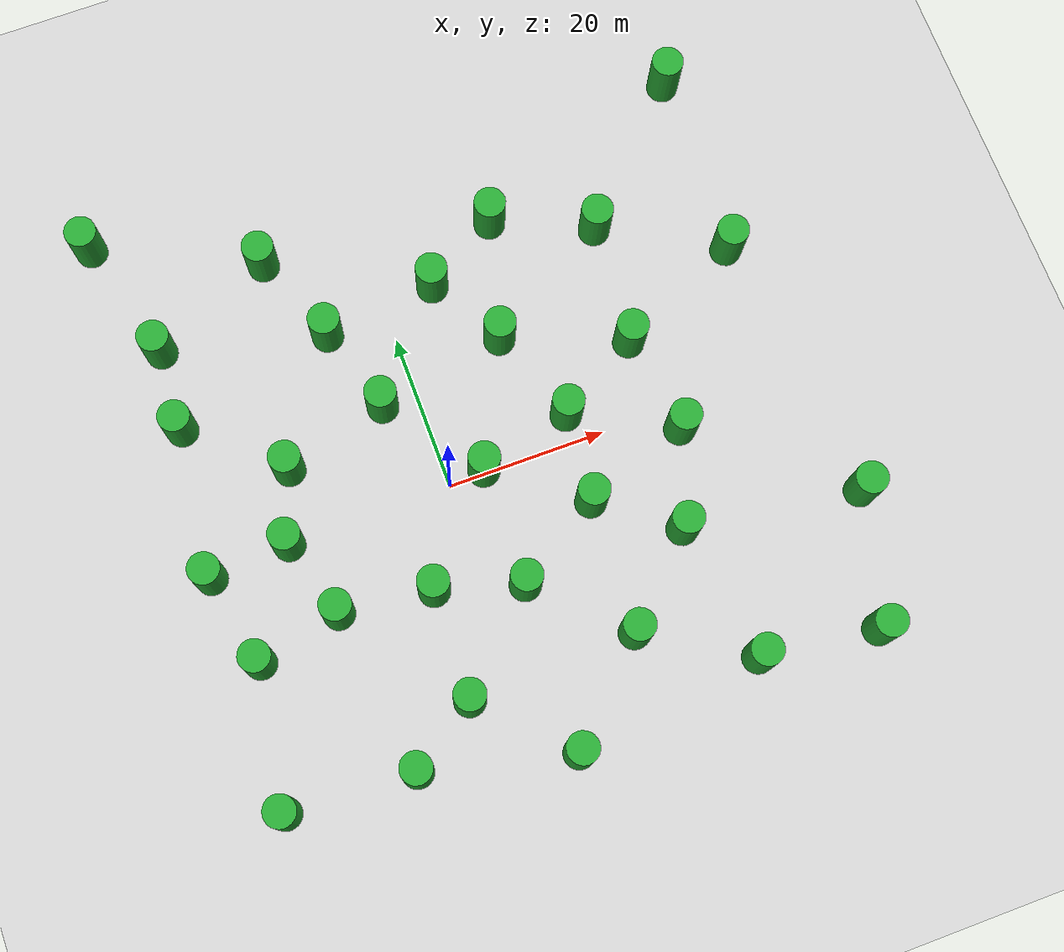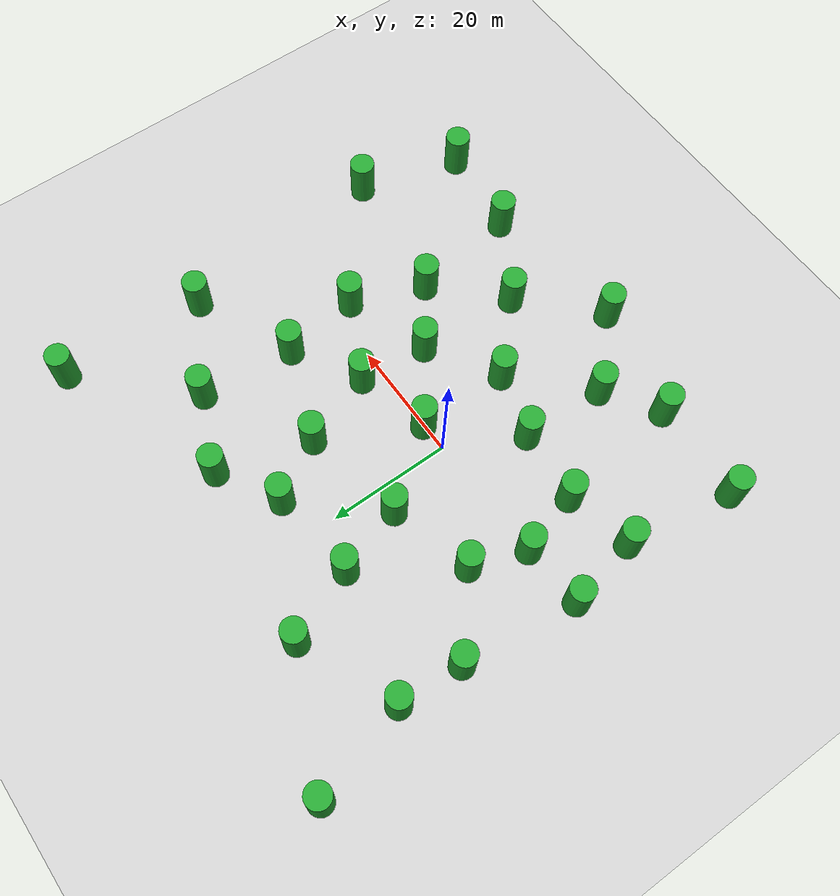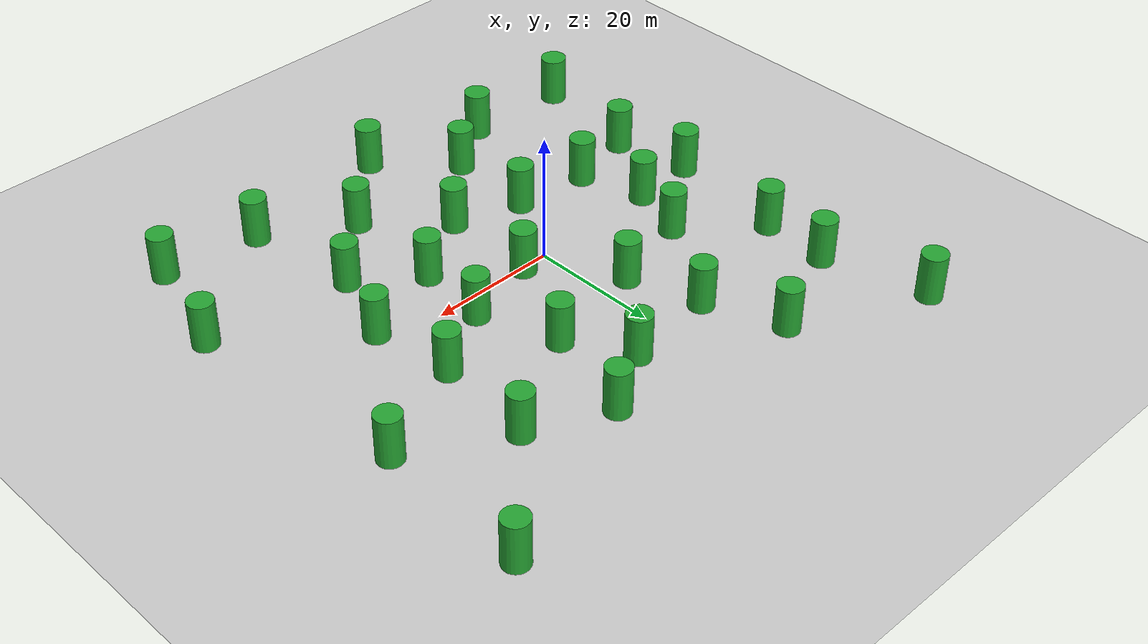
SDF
<sdf version="1.7">
 <world name="default">
  <plugin name="gazebo_ros_state" filename="libgazebo_ros_state.so">
   <ros>
    <namespace>/plug</namespace>
    <argument>model_states:=model_states_plug</argument>
    <argument>link_states:=link_states_plug</argument>
   </ros>
   <update_rate>100.0</update_rate>
  </plugin>
  <plugin name="disable_physics" filename="libdisable_physics.so"/>
  <light name="sun" type="directional">
   <pose>0 0 10 0 -0 0</pose>
   <diffuse>0.8 0.8 0.8 1</diffuse>
   <specular>0.2 0.2 0.2 1</specular>
   <attenuation>
    <range>1000</range>
    <constant>0.9</constant>
    <linear>0.01</linear>
    <quadratic>0.001</quadratic>
   </attenuation>
   <direction>-0.5 0.1 -0.9</direction>
   <spot><inner_angle>0</inner_angle><outer_angle>0</outer_angle><falloff>0</falloff></spot>
  </light>
  <model name="ground_plane">
   <static>1</static>
   <link name="link">
    <collision name="collision">
     <geometry><plane><normal>0 0 1</normal><size>100 100</size></plane></geometry>
     <surface>
      <contact><collide_bitmask>65535</collide_bitmask></contact>
      <friction><ode><mu>100</mu><mu2>50</mu2></ode></friction>
     </surface>
    </collision>
    <visual name="visual">
     <cast_shadows>0</cast_shadows>
     <geometry><plane><normal>0 0 1</normal><size>100 100</size></plane></geometry>
     <material>
      <script><uri>file://media/materials/scripts/gazebo.material</uri><name>Gazebo/Grey</name></script>
     </material>
    </visual>
   </link>
  </model>
  <gravity>0 0 -9.8</gravity>
  <magnetic_field>6e-06 2.3e-05 -4.2e-05</magnetic_field>
  <atmosphere type="adiabatic"/>
  <physics type="ode">
   <max_step_size>0.01</max_step_size>
   <real_time_factor>1</real_time_factor>
   <real_time_update_rate>100</real_time_update_rate>
  </physics>
  <scene><ambient>0.4 0.4 0.4 1</ambient><background>0.7 0.7 0.7 1</background><shadows>1</shadows></scene>
  <audio><device>default</device></audio>
  <spherical_coordinates>
   <surface_model>EARTH_WGS84</surface_model>
   <latitude_deg>0</latitude_deg>
   <longitude_deg>0</longitude_deg>
   <elevation>0</elevation>
   <heading_deg>0</heading_deg>
  </spherical_coordinates>
  <model name="unit_cylinder_green_2_clone">
   <link name="link">
    <inertial>
     <mass>1</mass>
     <inertia><ixx>0.145833</ixx><ixy>0</ixy><ixz>0</ixz><iyy>0.145833</iyy><iyz>0</iyz><izz>0.125</izz></inertia>
    </inertial>
    <visual name="visual">
     <geometry><cylinder><radius>2</radius><length>10</length></cylinder></geometry>
     <material>
      <script><name>Gazebo/Green</name><uri>file://media/materials/scripts/gazebo.material</uri></script>
      <shader type="pixel"><normal_map>__default__</normal_map></shader>
      <ambient>0 1 0.3 1</ambient>
      <diffuse>0.7 0.7 0.7 1</diffuse>
      <specular>0.01 0.01 0.01 1</specular>
      <emissive>0 0 0 1</emissive>
     </material>
    </visual>
    <collision name="collision">
     <geometry><cylinder><radius>2</radius><length>5</length></cylinder></geometry>
     <surface>
      <friction>
       <ode><mu>1</mu><mu2>1</mu2><fdir1>0 0 0</fdir1><slip1>0</slip1><slip2>0</slip2></ode>
       <torsional>
        <coefficient>1</coefficient>
        <patch_radius>0</patch_radius>
        <surface_radius>0</surface_radius>
        <use_patch_radius>1</use_patch_radius>
        <ode><slip>0</slip></ode>
       </torsional>
      </friction>
      <bounce><restitution_coefficient>0</restitution_coefficient><threshold>1e+06</threshold></bounce>
      <contact>
       <collide_without_contact>0</collide_without_contact>
       <collide_without_contact_bitmask>1</collide_without_contact_bitmask>
       <collide_bitmask>1</collide_bitmask>
       <ode>
        <soft_cfm>0</soft_cfm>
        <soft_erp>0.2</soft_erp>
        <kp>1e+13</kp>
        <kd>1</kd>
        <max_vel>0.01</max_vel>
        <min_depth>0</min_depth>
       </ode>
       <bullet>
        <split_impulse>1</split_impulse>
        <split_impulse_penetration_threshold>-0.01</split_impulse_penetration_threshold>
        <soft_cfm>0</soft_cfm>
        <soft_erp>0.2</soft_erp>
        <kp>1e+13</kp>
        <kd>1</kd>
       </bullet>
      </contact>
     </surface>
    </collision>
   </link>
   <static>0</static>
   <pose>-6.19288 -11.5757 2.49999 0 0 -0.000968</pose>
  </model>
  <model name="unit_cylinder_green_2_clone_0">
   <link name="link">
    <inertial>
     <mass>1</mass>
     <inertia><ixx>0.145833</ixx><ixy>0</ixy><ixz>0</ixz><iyy>0.145833</iyy><iyz>0</iyz><izz>0.125</izz></inertia>
    </inertial>
    <visual name="visual">
     <geometry><cylinder><radius>2</radius><length>10</length></cylinder></geometry>
     <material>
      <script><name>Gazebo/Green</name><uri>file://media/materials/scripts/gazebo.material</uri></script>
      <shader type="pixel"><normal_map>__default__</normal_map></shader>
      <ambient>0 1 0.3 1</ambient>
      <diffuse>0.7 0.7 0.7 1</diffuse>
      <specular>0.01 0.01 0.01 1</specular>
      <emissive>0 0 0 1</emissive>
     </material>
    </visual>
    <collision name="collision">
     <geometry><cylinder><radius>2</radius><length>5</length></cylinder></geometry>
     <surface>
      <friction>
       <ode><mu>1</mu><mu2>1</mu2><fdir1>0 0 0</fdir1><slip1>0</slip1><slip2>0</slip2></ode>
       <torsional>
        <coefficient>1</coefficient>
        <patch_radius>0</patch_radius>
        <surface_radius>0</surface_radius>
        <use_patch_radius>1</use_patch_radius>
        <ode><slip>0</slip></ode>
       </torsional>
      </friction>
      <bounce><restitution_coefficient>0</restitution_coefficient><threshold>1e+06</threshold></bounce>
      <contact>
       <collide_without_contact>0</collide_without_contact>
       <collide_without_contact_bitmask>1</collide_without_contact_bitmask>
       <collide_bitmask>1</collide_bitmask>
       <ode>
        <soft_cfm>0</soft_cfm>
        <soft_erp>0.2</soft_erp>
        <kp>1e+13</kp>
        <kd>1</kd>
        <max_vel>0.01</max_vel>
        <min_depth>0</min_depth>
       </ode>
       <bullet>
        <split_impulse>1</split_impulse>
        <split_impulse_penetration_threshold>-0.01</split_impulse_penetration_threshold>
        <soft_cfm>0</soft_cfm>
        <soft_erp>0.2</soft_erp>
        <kp>1e+13</kp>
        <kd>1</kd>
       </bullet>
      </contact>
     </surface>
    </collision>
   </link>
   <static>0</static>
   <pose>-17.8904 -10.2821 2.49999 0 0 -0.000968</pose>
  </model>
  <model name="unit_cylinder_green_2_clone_1">
   <link name="link">
    <inertial>
     <mass>1</mass>
     <inertia><ixx>0.145833</ixx><ixy>0</ixy><ixz>0</ixz><iyy>0.145833</iyy><iyz>0</iyz><izz>0.125</izz></inertia>
    </inertial>
    <visual name="visual">
     <geometry><cylinder><radius>2</radius><length>10</length></cylinder></geometry>
     <material>
      <script><name>Gazebo/Green</name><uri>file://media/materials/scripts/gazebo.material</uri></script>
      <shader type="pixel"><normal_map>__default__</normal_map></shader>
      <ambient>0 1 0.3 1</ambient>
      <diffuse>0.7 0.7 0.7 1</diffuse>
      <specular>0.01 0.01 0.01 1</specular>
      <emissive>0 0 0 1</emissive>
     </material>
    </visual>
    <collision name="collision">
     <geometry><cylinder><radius>2</radius><length>5</length></cylinder></geometry>
     <surface>
      <friction>
       <ode><mu>1</mu><mu2>1</mu2><fdir1>0 0 0</fdir1><slip1>0</slip1><slip2>0</slip2></ode>
       <torsional>
        <coefficient>1</coefficient>
        <patch_radius>0</patch_radius>
        <surface_radius>0</surface_radius>
        <use_patch_radius>1</use_patch_radius>
        <ode><slip>0</slip></ode>
       </torsional>
      </friction>
      <bounce><restitution_coefficient>0</restitution_coefficient><threshold>1e+06</threshold></bounce>
      <contact>
       <collide_without_contact>0</collide_without_contact>
       <collide_without_contact_bitmask>1</collide_without_contact_bitmask>
       <collide_bitmask>1</collide_bitmask>
       <ode>
        <soft_cfm>0</soft_cfm>
        <soft_erp>0.2</soft_erp>
        <kp>1e+13</kp>
        <kd>1</kd>
        <max_vel>0.01</max_vel>
        <min_depth>0</min_depth>
       </ode>
       <bullet>
        <split_impulse>1</split_impulse>
        <split_impulse_penetration_threshold>-0.01</split_impulse_penetration_threshold>
        <soft_cfm>0</soft_cfm>
        <soft_erp>0.2</soft_erp>
        <kp>1e+13</kp>
        <kd>1</kd>
       </bullet>
      </contact>
     </surface>
    </collision>
   </link>
   <static>0</static>
   <pose>-17.8627 8.62007 2.49999 0 0 -0.000968</pose>
  </model>
  <model name="unit_cylinder_green_2_clone_2">
   <link name="link">
    <inertial>
     <mass>1</mass>
     <inertia><ixx>0.145833</ixx><ixy>0</ixy><ixz>0</ixz><iyy>0.145833</iyy><iyz>0</iyz><izz>0.125</izz></inertia>
    </inertial>
    <visual name="visual">
     <geometry><cylinder><radius>2</radius><length>10</length></cylinder></geometry>
     <material>
      <script><name>Gazebo/Green</name><uri>file://media/materials/scripts/gazebo.material</uri></script>
      <shader type="pixel"><normal_map>__default__</normal_map></shader>
      <ambient>0 1 0.3 1</ambient>
      <diffuse>0.7 0.7 0.7 1</diffuse>
      <specular>0.01 0.01 0.01 1</specular>
      <emissive>0 0 0 1</emissive>
     </material>
    </visual>
    <collision name="collision">
     <geometry><cylinder><radius>2</radius><length>5</length></cylinder></geometry>
     <surface>
      <friction>
       <ode><mu>1</mu><mu2>1</mu2><fdir1>0 0 0</fdir1><slip1>0</slip1><slip2>0</slip2></ode>
       <torsional>
        <coefficient>1</coefficient>
        <patch_radius>0</patch_radius>
        <surface_radius>0</surface_radius>
        <use_patch_radius>1</use_patch_radius>
        <ode><slip>0</slip></ode>
       </torsional>
      </friction>
      <bounce><restitution_coefficient>0</restitution_coefficient><threshold>1e+06</threshold></bounce>
      <contact>
       <collide_without_contact>0</collide_without_contact>
       <collide_without_contact_bitmask>1</collide_without_contact_bitmask>
       <collide_bitmask>1</collide_bitmask>
       <ode>
        <soft_cfm>0</soft_cfm>
        <soft_erp>0.2</soft_erp>
        <kp>1e+13</kp>
        <kd>1</kd>
        <max_vel>0.01</max_vel>
        <min_depth>0</min_depth>
       </ode>
       <bullet>
        <split_impulse>1</split_impulse>
        <split_impulse_penetration_threshold>-0.01</split_impulse_penetration_threshold>
        <soft_cfm>0</soft_cfm>
        <soft_erp>0.2</soft_erp>
        <kp>1e+13</kp>
        <kd>1</kd>
       </bullet>
      </contact>
     </surface>
    </collision>
   </link>
   <static>0</static>
   <pose>-20.8598 -0.277149 2.49999 0 0 -0.000968</pose>
  </model>
  <model name="unit_cylinder_green_2_clone_clone_2">
   <link name="link">
    <inertial>
     <mass>1</mass>
     <inertia><ixx>0.145833</ixx><ixy>0</ixy><ixz>0</ixz><iyy>0.145833</iyy><iyz>0</iyz><izz>0.125</izz></inertia>
    </inertial>
    <visual name="visual">
     <geometry><cylinder><radius>2</radius><length>10</length></cylinder></geometry>
     <material>
      <script><name>Gazebo/Green</name><uri>file://media/materials/scripts/gazebo.material</uri></script>
      <shader type="pixel"><normal_map>__default__</normal_map></shader>
      <ambient>0 1 0.3 1</ambient>
      <diffuse>0.7 0.7 0.7 1</diffuse>
      <specular>0.01 0.01 0.01 1</specular>
      <emissive>0 0 0 1</emissive>
     </material>
    </visual>
    <collision name="collision">
     <geometry><cylinder><radius>2</radius><length>5</length></cylinder></geometry>
     <surface>
      <friction>
       <ode><mu>1</mu><mu2>1</mu2><fdir1>0 0 0</fdir1><slip1>0</slip1><slip2>0</slip2></ode>
       <torsional>
        <coefficient>1</coefficient>
        <patch_radius>0</patch_radius>
        <surface_radius>0</surface_radius>
        <use_patch_radius>1</use_patch_radius>
        <ode><slip>0</slip></ode>
       </torsional>
      </friction>
      <bounce><restitution_coefficient>0</restitution_coefficient><threshold>1e+06</threshold></bounce>
      <contact>
       <collide_without_contact>0</collide_without_contact>
       <collide_without_contact_bitmask>1</collide_without_contact_bitmask>
       <collide_bitmask>1</collide_bitmask>
       <ode>
        <soft_cfm>0</soft_cfm>
        <soft_erp>0.2</soft_erp>
        <kp>1e+13</kp>
        <kd>1</kd>
        <max_vel>0.01</max_vel>
        <min_depth>0</min_depth>
       </ode>
       <bullet>
        <split_impulse>1</split_impulse>
        <split_impulse_penetration_threshold>-0.01</split_impulse_penetration_threshold>
        <soft_cfm>0</soft_cfm>
        <soft_erp>0.2</soft_erp>
        <kp>1e+13</kp>
        <kd>1</kd>
       </bullet>
      </contact>
     </surface>
    </collision>
   </link>
   <static>0</static>
   <pose>-4.45496 12.3058 2.49999 0 0 -0.000967</pose>
  </model>
  <model name="unit_cylinder_green_2_clone_clone_3">
   <link name="link">
    <inertial>
     <mass>1</mass>
     <inertia><ixx>0.145833</ixx><ixy>0</ixy><ixz>0</ixz><iyy>0.145833</iyy><iyz>0</iyz><izz>0.125</izz></inertia>
    </inertial>
    <visual name="visual">
     <geometry><cylinder><radius>2</radius><length>10</length></cylinder></geometry>
     <material>
      <script><name>Gazebo/Green</name><uri>file://media/materials/scripts/gazebo.material</uri></script>
      <shader type="pixel"><normal_map>__default__</normal_map></shader>
      <ambient>0 1 0.3 1</ambient>
      <diffuse>0.7 0.7 0.7 1</diffuse>
      <specular>0.01 0.01 0.01 1</specular>
      <emissive>0 0 0 1</emissive>
     </material>
    </visual>
    <collision name="collision">
     <geometry><cylinder><radius>2</radius><length>5</length></cylinder></geometry>
     <surface>
      <friction>
       <ode><mu>1</mu><mu2>1</mu2><fdir1>0 0 0</fdir1><slip1>0</slip1><slip2>0</slip2></ode>
       <torsional>
        <coefficient>1</coefficient>
        <patch_radius>0</patch_radius>
        <surface_radius>0</surface_radius>
        <use_patch_radius>1</use_patch_radius>
        <ode><slip>0</slip></ode>
       </torsional>
      </friction>
      <bounce><restitution_coefficient>0</restitution_coefficient><threshold>1e+06</threshold></bounce>
      <contact>
       <collide_without_contact>0</collide_without_contact>
       <collide_without_contact_bitmask>1</collide_without_contact_bitmask>
       <collide_bitmask>1</collide_bitmask>
       <ode>
        <soft_cfm>0</soft_cfm>
        <soft_erp>0.2</soft_erp>
        <kp>1e+13</kp>
        <kd>1</kd>
        <max_vel>0.01</max_vel>
        <min_depth>0</min_depth>
       </ode>
       <bullet>
        <split_impulse>1</split_impulse>
        <split_impulse_penetration_threshold>-0.01</split_impulse_penetration_threshold>
        <soft_cfm>0</soft_cfm>
        <soft_erp>0.2</soft_erp>
        <kp>1e+13</kp>
        <kd>1</kd>
       </bullet>
      </contact>
     </surface>
    </collision>
   </link>
   <static>0</static>
   <pose>4.54748 0.366271 2.49999 0 0 -0.000967</pose>
  </model>
  <model name="unit_cylinder_green_2_clone_clone_7">
   <link name="link">
    <inertial>
     <mass>1</mass>
     <inertia><ixx>0.145833</ixx><ixy>0</ixy><ixz>0</ixz><iyy>0.145833</iyy><iyz>0</iyz><izz>0.125</izz></inertia>
    </inertial>
    <visual name="visual">
     <geometry><cylinder><radius>2</radius><length>10</length></cylinder></geometry>
     <material>
      <script><name>Gazebo/Green</name><uri>file://media/materials/scripts/gazebo.material</uri></script>
      <shader type="pixel"><normal_map>__default__</normal_map></shader>
      <ambient>0 1 0.3 1</ambient>
      <diffuse>0.7 0.7 0.7 1</diffuse>
      <specular>0.01 0.01 0.01 1</specular>
      <emissive>0 0 0 1</emissive>
     </material>
    </visual>
    <collision name="collision">
     <geometry><cylinder><radius>2</radius><length>5</length></cylinder></geometry>
     <surface>
      <friction>
       <ode><mu>1</mu><mu2>1</mu2><fdir1>0 0 0</fdir1><slip1>0</slip1><slip2>0</slip2></ode>
       <torsional>
        <coefficient>1</coefficient>
        <patch_radius>0</patch_radius>
        <surface_radius>0</surface_radius>
        <use_patch_radius>1</use_patch_radius>
        <ode><slip>0</slip></ode>
       </torsional>
      </friction>
      <bounce><restitution_coefficient>0</restitution_coefficient><threshold>1e+06</threshold></bounce>
      <contact>
       <collide_without_contact>0</collide_without_contact>
       <collide_without_contact_bitmask>1</collide_without_contact_bitmask>
       <collide_bitmask>1</collide_bitmask>
       <ode>
        <soft_cfm>0</soft_cfm>
        <soft_erp>0.2</soft_erp>
        <kp>1e+13</kp>
        <kd>1</kd>
        <max_vel>0.01</max_vel>
        <min_depth>0</min_depth>
       </ode>
       <bullet>
        <split_impulse>1</split_impulse>
        <split_impulse_penetration_threshold>-0.01</split_impulse_penetration_threshold>
        <soft_cfm>0</soft_cfm>
        <soft_erp>0.2</soft_erp>
        <kp>1e+13</kp>
        <kd>1</kd>
       </bullet>
      </contact>
     </surface>
    </collision>
   </link>
   <static>0</static>
   <pose>-31 -1 2.49999 0 0 -0.000967</pose>
  </model>
  <model name="unit_cylinder_green_2_clone_clone_8">
   <link name="link">
    <inertial>
     <mass>1</mass>
     <inertia><ixx>0.145833</ixx><ixy>0</ixy><ixz>0</ixz><iyy>0.145833</iyy><iyz>0</iyz><izz>0.125</izz></inertia>
    </inertial>
    <visual name="visual">
     <geometry><cylinder><radius>2</radius><length>10</length></cylinder></geometry>
     <material>
      <script><name>Gazebo/Green</name><uri>file://media/materials/scripts/gazebo.material</uri></script>
      <shader type="pixel"><normal_map>__default__</normal_map></shader>
      <ambient>0 1 0.3 1</ambient>
      <diffuse>0.7 0.7 0.7 1</diffuse>
      <specular>0.01 0.01 0.01 1</specular>
      <emissive>0 0 0 1</emissive>
     </material>
    </visual>
    <collision name="collision">
     <geometry><cylinder><radius>2</radius><length>5</length></cylinder></geometry>
     <surface>
      <friction>
       <ode><mu>1</mu><mu2>1</mu2><fdir1>0 0 0</fdir1><slip1>0</slip1><slip2>0</slip2></ode>
       <torsional>
        <coefficient>1</coefficient>
        <patch_radius>0</patch_radius>
        <surface_radius>0</surface_radius>
        <use_patch_radius>1</use_patch_radius>
        <ode><slip>0</slip></ode>
       </torsional>
      </friction>
      <bounce><restitution_coefficient>0</restitution_coefficient><threshold>1e+06</threshold></bounce>
      <contact>
       <collide_without_contact>0</collide_without_contact>
       <collide_without_contact_bitmask>1</collide_without_contact_bitmask>
       <collide_bitmask>1</collide_bitmask>
       <ode>
        <soft_cfm>0</soft_cfm>
        <soft_erp>0.2</soft_erp>
        <kp>1e+13</kp>
        <kd>1</kd>
        <max_vel>0.01</max_vel>
        <min_depth>0</min_depth>
       </ode>
       <bullet>
        <split_impulse>1</split_impulse>
        <split_impulse_penetration_threshold>-0.01</split_impulse_penetration_threshold>
        <soft_cfm>0</soft_cfm>
        <soft_erp>0.2</soft_erp>
        <kp>1e+13</kp>
        <kd>1</kd>
       </bullet>
      </contact>
     </surface>
    </collision>
   </link>
   <static>0</static>
   <pose>-28.7386 17.9151 2.49999 0 0 -0.000967</pose>
  </model>
  <model name="unit_cylinder_green_2_clone_clone_9">
   <link name="link">
    <inertial>
     <mass>1</mass>
     <inertia><ixx>0.145833</ixx><ixy>0</ixy><ixz>0</ixz><iyy>0.145833</iyy><iyz>0</iyz><izz>0.125</izz></inertia>
    </inertial>
    <visual name="visual">
     <geometry><cylinder><radius>2</radius><length>10</length></cylinder></geometry>
     <material>
      <script><name>Gazebo/Green</name><uri>file://media/materials/scripts/gazebo.material</uri></script>
      <shader type="pixel"><normal_map>__default__</normal_map></shader>
      <ambient>0 1 0.3 1</ambient>
      <diffuse>0.7 0.7 0.7 1</diffuse>
      <specular>0.01 0.01 0.01 1</specular>
      <emissive>0 0 0 1</emissive>
     </material>
    </visual>
    <collision name="collision">
     <geometry><cylinder><radius>2</radius><length>5</length></cylinder></geometry>
     <surface>
      <friction>
       <ode><mu>1</mu><mu2>1</mu2><fdir1>0 0 0</fdir1><slip1>0</slip1><slip2>0</slip2></ode>
       <torsional>
        <coefficient>1</coefficient>
        <patch_radius>0</patch_radius>
        <surface_radius>0</surface_radius>
        <use_patch_radius>1</use_patch_radius>
        <ode><slip>0</slip></ode>
       </torsional>
      </friction>
      <bounce><restitution_coefficient>0</restitution_coefficient><threshold>1e+06</threshold></bounce>
      <contact>
       <collide_without_contact>0</collide_without_contact>
       <collide_without_contact_bitmask>1</collide_without_contact_bitmask>
       <collide_bitmask>1</collide_bitmask>
       <ode>
        <soft_cfm>0</soft_cfm>
        <soft_erp>0.2</soft_erp>
        <kp>1e+13</kp>
        <kd>1</kd>
        <max_vel>0.01</max_vel>
        <min_depth>0</min_depth>
       </ode>
       <bullet>
        <split_impulse>1</split_impulse>
        <split_impulse_penetration_threshold>-0.01</split_impulse_penetration_threshold>
        <soft_cfm>0</soft_cfm>
        <soft_erp>0.2</soft_erp>
        <kp>1e+13</kp>
        <kd>1</kd>
       </bullet>
      </contact>
     </surface>
    </collision>
   </link>
   <static>0</static>
   <pose>-12.5558 35.0798 2.49999 0 0 -0.000967</pose>
  </model>
  <model name="unit_cylinder_green_2_clone_clone_10">
   <link name="link">
    <inertial>
     <mass>1</mass>
     <inertia><ixx>0.145833</ixx><ixy>0</ixy><ixz>0</ixz><iyy>0.145833</iyy><iyz>0</iyz><izz>0.125</izz></inertia>
    </inertial>
    <visual name="visual">
     <geometry><cylinder><radius>2</radius><length>10</length></cylinder></geometry>
     <material>
      <script><name>Gazebo/Green</name><uri>file://media/materials/scripts/gazebo.material</uri></script>
      <shader type="pixel"><normal_map>__default__</normal_map></shader>
      <ambient>0 1 0.3 1</ambient>
      <diffuse>0.7 0.7 0.7 1</diffuse>
      <specular>0.01 0.01 0.01 1</specular>
      <emissive>0 0 0 1</emissive>
     </material>
    </visual>
    <collision name="collision">
     <geometry><cylinder><radius>2</radius><length>5</length></cylinder></geometry>
     <surface>
      <friction>
       <ode><mu>1</mu><mu2>1</mu2><fdir1>0 0 0</fdir1><slip1>0</slip1><slip2>0</slip2></ode>
       <torsional>
        <coefficient>1</coefficient>
        <patch_radius>0</patch_radius>
        <surface_radius>0</surface_radius>
        <use_patch_radius>1</use_patch_radius>
        <ode><slip>0</slip></ode>
       </torsional>
      </friction>
      <bounce><restitution_coefficient>0</restitution_coefficient><threshold>1e+06</threshold></bounce>
      <contact>
       <collide_without_contact>0</collide_without_contact>
       <collide_without_contact_bitmask>1</collide_without_contact_bitmask>
       <collide_bitmask>1</collide_bitmask>
       <ode>
        <soft_cfm>0</soft_cfm>
        <soft_erp>0.2</soft_erp>
        <kp>1e+13</kp>
        <kd>1</kd>
        <max_vel>0.01</max_vel>
        <min_depth>0</min_depth>
       </ode>
       <bullet>
        <split_impulse>1</split_impulse>
        <split_impulse_penetration_threshold>-0.01</split_impulse_penetration_threshold>
        <soft_cfm>0</soft_cfm>
        <soft_erp>0.2</soft_erp>
        <kp>1e+13</kp>
        <kd>1</kd>
       </bullet>
      </contact>
     </surface>
    </collision>
   </link>
   <static>0</static>
   <pose>-7.89767 23.435 2.49999 0 0 -0.000967</pose>
  </model>
  <model name="unit_cylinder_green_2_clone_clone_11">
   <link name="link">
    <inertial>
     <mass>1</mass>
     <inertia><ixx>0.145833</ixx><ixy>0</ixy><ixz>0</ixz><iyy>0.145833</iyy><iyz>0</iyz><izz>0.125</izz></inertia>
    </inertial>
    <visual name="visual">
     <geometry><cylinder><radius>2</radius><length>10</length></cylinder></geometry>
     <material>
      <script><name>Gazebo/Green</name><uri>file://media/materials/scripts/gazebo.material</uri></script>
      <shader type="pixel"><normal_map>__default__</normal_map></shader>
      <ambient>0 1 0.3 1</ambient>
      <diffuse>0.7 0.7 0.7 1</diffuse>
      <specular>0.01 0.01 0.01 1</specular>
      <emissive>0 0 0 1</emissive>
     </material>
    </visual>
    <collision name="collision">
     <geometry><cylinder><radius>2</radius><length>5</length></cylinder></geometry>
     <surface>
      <friction>
       <ode><mu>1</mu><mu2>1</mu2><fdir1>0 0 0</fdir1><slip1>0</slip1><slip2>0</slip2></ode>
       <torsional>
        <coefficient>1</coefficient>
        <patch_radius>0</patch_radius>
        <surface_radius>0</surface_radius>
        <use_patch_radius>1</use_patch_radius>
        <ode><slip>0</slip></ode>
       </torsional>
      </friction>
      <bounce><restitution_coefficient>0</restitution_coefficient><threshold>1e+06</threshold></bounce>
      <contact>
       <collide_without_contact>0</collide_without_contact>
       <collide_without_contact_bitmask>1</collide_without_contact_bitmask>
       <collide_bitmask>1</collide_bitmask>
       <ode>
        <soft_cfm>0</soft_cfm>
        <soft_erp>0.2</soft_erp>
        <kp>1e+13</kp>
        <kd>1</kd>
        <max_vel>0.01</max_vel>
        <min_depth>0</min_depth>
       </ode>
       <bullet>
        <split_impulse>1</split_impulse>
        <split_impulse_penetration_threshold>-0.01</split_impulse_penetration_threshold>
        <soft_cfm>0</soft_cfm>
        <soft_erp>0.2</soft_erp>
        <kp>1e+13</kp>
        <kd>1</kd>
       </bullet>
      </contact>
     </surface>
    </collision>
   </link>
   <static>0</static>
   <pose>6.6281 25.0703 2.49999 0 0 -0.000967</pose>
  </model>
  <model name="unit_cylinder_green_2_clone_clone_13">
   <link name="link">
    <inertial>
     <mass>1</mass>
     <inertia><ixx>0.145833</ixx><ixy>0</ixy><ixz>0</ixz><iyy>0.145833</iyy><iyz>0</iyz><izz>0.125</izz></inertia>
    </inertial>
    <visual name="visual">
     <geometry><cylinder><radius>2</radius><length>10</length></cylinder></geometry>
     <material>
      <script><name>Gazebo/Green</name><uri>file://media/materials/scripts/gazebo.material</uri></script>
      <shader type="pixel"><normal_map>__default__</normal_map></shader>
      <ambient>0 1 0.3 1</ambient>
      <diffuse>0.7 0.7 0.7 1</diffuse>
      <specular>0.01 0.01 0.01 1</specular>
      <emissive>0 0 0 1</emissive>
     </material>
    </visual>
    <collision name="collision">
     <geometry><cylinder><radius>2</radius><length>5</length></cylinder></geometry>
     <surface>
      <friction>
       <ode><mu>1</mu><mu2>1</mu2><fdir1>0 0 0</fdir1><slip1>0</slip1><slip2>0</slip2></ode>
       <torsional>
        <coefficient>1</coefficient>
        <patch_radius>0</patch_radius>
        <surface_radius>0</surface_radius>
        <use_patch_radius>1</use_patch_radius>
        <ode><slip>0</slip></ode>
       </torsional>
      </friction>
      <bounce><restitution_coefficient>0</restitution_coefficient><threshold>1e+06</threshold></bounce>
      <contact>
       <collide_without_contact>0</collide_without_contact>
       <collide_without_contact_bitmask>1</collide_without_contact_bitmask>
       <collide_bitmask>1</collide_bitmask>
       <ode>
        <soft_cfm>0</soft_cfm>
        <soft_erp>0.2</soft_erp>
        <kp>1e+13</kp>
        <kd>1</kd>
        <max_vel>0.01</max_vel>
        <min_depth>0</min_depth>
       </ode>
       <bullet>
        <split_impulse>1</split_impulse>
        <split_impulse_penetration_threshold>-0.01</split_impulse_penetration_threshold>
        <soft_cfm>0</soft_cfm>
        <soft_erp>0.2</soft_erp>
        <kp>1e+13</kp>
        <kd>1</kd>
       </bullet>
      </contact>
     </surface>
    </collision>
   </link>
   <static>0</static>
   <pose>-28.5894 -12.7369 2.49999 0 0 -0.000967</pose>
  </model>
  <model name="unit_cylinder_green_2_clone_clone_14">
   <link name="link">
    <inertial>
     <mass>1</mass>
     <inertia><ixx>0.145833</ixx><ixy>0</ixy><ixz>0</ixz><iyy>0.145833</iyy><iyz>0</iyz><izz>0.125</izz></inertia>
    </inertial>
    <visual name="visual">
     <geometry><cylinder><radius>2</radius><length>10</length></cylinder></geometry>
     <material>
      <script><name>Gazebo/Green</name><uri>file://media/materials/scripts/gazebo.material</uri></script>
      <shader type="pixel"><normal_map>__default__</normal_map></shader>
      <ambient>0 1 0.3 1</ambient>
      <diffuse>0.7 0.7 0.7 1</diffuse>
      <specular>0.01 0.01 0.01 1</specular>
      <emissive>0 0 0 1</emissive>
     </material>
    </visual>
    <collision name="collision">
     <geometry><cylinder><radius>2</radius><length>5</length></cylinder></geometry>
     <surface>
      <friction>
       <ode><mu>1</mu><mu2>1</mu2><fdir1>0 0 0</fdir1><slip1>0</slip1><slip2>0</slip2></ode>
       <torsional>
        <coefficient>1</coefficient>
        <patch_radius>0</patch_radius>
        <surface_radius>0</surface_radius>
        <use_patch_radius>1</use_patch_radius>
        <ode><slip>0</slip></ode>
       </torsional>
      </friction>
      <bounce><restitution_coefficient>0</restitution_coefficient><threshold>1e+06</threshold></bounce>
      <contact>
       <collide_without_contact>0</collide_without_contact>
       <collide_without_contact_bitmask>1</collide_without_contact_bitmask>
       <collide_bitmask>1</collide_bitmask>
       <ode>
        <soft_cfm>0</soft_cfm>
        <soft_erp>0.2</soft_erp>
        <kp>1e+13</kp>
        <kd>1</kd>
        <max_vel>0.01</max_vel>
        <min_depth>0</min_depth>
       </ode>
       <bullet>
        <split_impulse>1</split_impulse>
        <split_impulse_penetration_threshold>-0.01</split_impulse_penetration_threshold>
        <soft_cfm>0</soft_cfm>
        <soft_erp>0.2</soft_erp>
        <kp>1e+13</kp>
        <kd>1</kd>
       </bullet>
      </contact>
     </surface>
    </collision>
   </link>
   <static>0</static>
   <pose>-28.1415 28.4335 2.49999 0 0 -0.000967</pose>
  </model>
  <model name="unit_cylinder_green_2_clone_clone_15">
   <link name="link">
    <inertial>
     <mass>1</mass>
     <inertia><ixx>0.145833</ixx><ixy>0</ixy><ixz>0</ixz><iyy>0.145833</iyy><iyz>0</iyz><izz>0.125</izz></inertia>
    </inertial>
    <visual name="visual">
     <geometry><cylinder><radius>2</radius><length>10</length></cylinder></geometry>
     <material>
      <script><name>Gazebo/Green</name><uri>file://media/materials/scripts/gazebo.material</uri></script>
      <shader type="pixel"><normal_map>__default__</normal_map></shader>
      <ambient>0 1 0.3 1</ambient>
      <diffuse>0.7 0.7 0.7 1</diffuse>
      <specular>0.01 0.01 0.01 1</specular>
      <emissive>0 0 0 1</emissive>
     </material>
    </visual>
    <collision name="collision">
     <geometry><cylinder><radius>2</radius><length>5</length></cylinder></geometry>
     <surface>
      <friction>
       <ode><mu>1</mu><mu2>1</mu2><fdir1>0 0 0</fdir1><slip1>0</slip1><slip2>0</slip2></ode>
       <torsional>
        <coefficient>1</coefficient>
        <patch_radius>0</patch_radius>
        <surface_radius>0</surface_radius>
        <use_patch_radius>1</use_patch_radius>
        <ode><slip>0</slip></ode>
       </torsional>
      </friction>
      <bounce><restitution_coefficient>0</restitution_coefficient><threshold>1e+06</threshold></bounce>
      <contact>
       <collide_without_contact>0</collide_without_contact>
       <collide_without_contact_bitmask>1</collide_without_contact_bitmask>
       <collide_bitmask>1</collide_bitmask>
       <ode>
        <soft_cfm>0</soft_cfm>
        <soft_erp>0.2</soft_erp>
        <kp>1e+13</kp>
        <kd>1</kd>
        <max_vel>0.01</max_vel>
        <min_depth>0</min_depth>
       </ode>
       <bullet>
        <split_impulse>1</split_impulse>
        <split_impulse_penetration_threshold>-0.01</split_impulse_penetration_threshold>
        <soft_cfm>0</soft_cfm>
        <soft_erp>0.2</soft_erp>
        <kp>1e+13</kp>
        <kd>1</kd>
       </bullet>
      </contact>
     </surface>
    </collision>
   </link>
   <static>0</static>
   <pose>4.37271 -14.6733 2.49999 0 0 -0.000967</pose>
  </model>
  <model name="unit_cylinder_green_2_clone_clone_16">
   <link name="link">
    <inertial>
     <mass>1</mass>
     <inertia><ixx>0.145833</ixx><ixy>0</ixy><ixz>0</ixz><iyy>0.145833</iyy><iyz>0</iyz><izz>0.125</izz></inertia>
    </inertial>
    <visual name="visual">
     <geometry><cylinder><radius>2</radius><length>10</length></cylinder></geometry>
     <material>
      <script><name>Gazebo/Green</name><uri>file://media/materials/scripts/gazebo.material</uri></script>
      <shader type="pixel"><normal_map>__default__</normal_map></shader>
      <ambient>0 1 0.3 1</ambient>
      <diffuse>0.7 0.7 0.7 1</diffuse>
      <specular>0.01 0.01 0.01 1</specular>
      <emissive>0 0 0 1</emissive>
     </material>
    </visual>
    <collision name="collision">
     <geometry><cylinder><radius>2</radius><length>5</length></cylinder></geometry>
     <surface>
      <friction>
       <ode><mu>1</mu><mu2>1</mu2><fdir1>0 0 0</fdir1><slip1>0</slip1><slip2>0</slip2></ode>
       <torsional>
        <coefficient>1</coefficient>
        <patch_radius>0</patch_radius>
        <surface_radius>0</surface_radius>
        <use_patch_radius>1</use_patch_radius>
        <ode><slip>0</slip></ode>
       </torsional>
      </friction>
      <bounce><restitution_coefficient>0</restitution_coefficient><threshold>1e+06</threshold></bounce>
      <contact>
       <collide_without_contact>0</collide_without_contact>
       <collide_without_contact_bitmask>1</collide_without_contact_bitmask>
       <collide_bitmask>1</collide_bitmask>
       <ode>
        <soft_cfm>0</soft_cfm>
        <soft_erp>0.2</soft_erp>
        <kp>1e+13</kp>
        <kd>1</kd>
        <max_vel>0.01</max_vel>
        <min_depth>0</min_depth>
       </ode>
       <bullet>
        <split_impulse>1</split_impulse>
        <split_impulse_penetration_threshold>-0.01</split_impulse_penetration_threshold>
        <soft_cfm>0</soft_cfm>
        <soft_erp>0.2</soft_erp>
        <kp>1e+13</kp>
        <kd>1</kd>
       </bullet>
      </contact>
     </surface>
    </collision>
   </link>
   <static>0</static>
   <pose>15.4924 -7.74923 2.49999 0 0 -0.000967</pose>
  </model>
  <model name="unit_cylinder_green_2_clone_clone_17">
   <link name="link">
    <inertial>
     <mass>1</mass>
     <inertia><ixx>0.145833</ixx><ixy>0</ixy><ixz>0</ixz><iyy>0.145833</iyy><iyz>0</iyz><izz>0.125</izz></inertia>
    </inertial>
    <visual name="visual">
     <geometry><cylinder><radius>2</radius><length>10</length></cylinder></geometry>
     <material>
      <script><name>Gazebo/Green</name><uri>file://media/materials/scripts/gazebo.material</uri></script>
      <shader type="pixel"><normal_map>__default__</normal_map></shader>
      <ambient>0 1 0.3 1</ambient>
      <diffuse>0.7 0.7 0.7 1</diffuse>
      <specular>0.01 0.01 0.01 1</specular>
      <emissive>0 0 0 1</emissive>
     </material>
    </visual>
    <collision name="collision">
     <geometry><cylinder><radius>2</radius><length>5</length></cylinder></geometry>
     <surface>
      <friction>
       <ode><mu>1</mu><mu2>1</mu2><fdir1>0 0 0</fdir1><slip1>0</slip1><slip2>0</slip2></ode>
       <torsional>
        <coefficient>1</coefficient>
        <patch_radius>0</patch_radius>
        <surface_radius>0</surface_radius>
        <use_patch_radius>1</use_patch_radius>
        <ode><slip>0</slip></ode>
       </torsional>
      </friction>
      <bounce><restitution_coefficient>0</restitution_coefficient><threshold>1e+06</threshold></bounce>
      <contact>
       <collide_without_contact>0</collide_without_contact>
       <collide_without_contact_bitmask>1</collide_without_contact_bitmask>
       <collide_bitmask>1</collide_bitmask>
       <ode>
        <soft_cfm>0</soft_cfm>
        <soft_erp>0.2</soft_erp>
        <kp>1e+13</kp>
        <kd>1</kd>
        <max_vel>0.01</max_vel>
        <min_depth>0</min_depth>
       </ode>
       <bullet>
        <split_impulse>1</split_impulse>
        <split_impulse_penetration_threshold>-0.01</split_impulse_penetration_threshold>
        <soft_cfm>0</soft_cfm>
        <soft_erp>0.2</soft_erp>
        <kp>1e+13</kp>
        <kd>1</kd>
       </bullet>
      </contact>
     </surface>
    </collision>
   </link>
   <static>0</static>
   <pose>16.5379 3.56067 2.49999 0 0 -0.000967</pose>
  </model>
  <model name="unit_cylinder_green_2_clone_clone_18">
   <link name="link">
    <inertial>
     <mass>1</mass>
     <inertia><ixx>0.145833</ixx><ixy>0</ixy><ixz>0</ixz><iyy>0.145833</iyy><iyz>0</iyz><izz>0.125</izz></inertia>
    </inertial>
    <visual name="visual">
     <geometry><cylinder><radius>2</radius><length>10</length></cylinder></geometry>
     <material>
      <script><name>Gazebo/Green</name><uri>file://media/materials/scripts/gazebo.material</uri></script>
      <shader type="pixel"><normal_map>__default__</normal_map></shader>
      <ambient>0 1 0.3 1</ambient>
      <diffuse>0.7 0.7 0.7 1</diffuse>
      <specular>0.01 0.01 0.01 1</specular>
      <emissive>0 0 0 1</emissive>
     </material>
    </visual>
    <collision name="collision">
     <geometry><cylinder><radius>2</radius><length>5</length></cylinder></geometry>
     <surface>
      <friction>
       <ode><mu>1</mu><mu2>1</mu2><fdir1>0 0 0</fdir1><slip1>0</slip1><slip2>0</slip2></ode>
       <torsional>
        <coefficient>1</coefficient>
        <patch_radius>0</patch_radius>
        <surface_radius>0</surface_radius>
        <use_patch_radius>1</use_patch_radius>
        <ode><slip>0</slip></ode>
       </torsional>
      </friction>
      <bounce><restitution_coefficient>0</restitution_coefficient><threshold>1e+06</threshold></bounce>
      <contact>
       <collide_without_contact>0</collide_without_contact>
       <collide_without_contact_bitmask>1</collide_without_contact_bitmask>
       <collide_bitmask>1</collide_bitmask>
       <ode>
        <soft_cfm>0</soft_cfm>
        <soft_erp>0.2</soft_erp>
        <kp>1e+13</kp>
        <kd>1</kd>
        <max_vel>0.01</max_vel>
        <min_depth>0</min_depth>
       </ode>
       <bullet>
        <split_impulse>1</split_impulse>
        <split_impulse_penetration_threshold>-0.01</split_impulse_penetration_threshold>
        <soft_cfm>0</soft_cfm>
        <soft_erp>0.2</soft_erp>
        <kp>1e+13</kp>
        <kd>1</kd>
       </bullet>
      </contact>
     </surface>
    </collision>
   </link>
   <static>0</static>
   <pose>12.1932 15.6703 2.49999 0 0 -0.000967</pose>
  </model>
  <model name="unit_cylinder_green_2_clone_clone_19">
   <link name="link">
    <inertial>
     <mass>1</mass>
     <inertia><ixx>0.145833</ixx><ixy>0</ixy><ixz>0</ixz><iyy>0.145833</iyy><iyz>0</iyz><izz>0.125</izz></inertia>
    </inertial>
    <visual name="visual">
     <geometry><cylinder><radius>2</radius><length>10</length></cylinder></geometry>
     <material>
      <script><name>Gazebo/Green</name><uri>file://media/materials/scripts/gazebo.material</uri></script>
      <shader type="pixel"><normal_map>__default__</normal_map></shader>
      <ambient>0 1 0.3 1</ambient>
      <diffuse>0.7 0.7 0.7 1</diffuse>
      <specular>0.01 0.01 0.01 1</specular>
      <emissive>0 0 0 1</emissive>
     </material>
    </visual>
    <collision name="collision">
     <geometry><cylinder><radius>2</radius><length>5</length></cylinder></geometry>
     <surface>
      <friction>
       <ode><mu>1</mu><mu2>1</mu2><fdir1>0 0 0</fdir1><slip1>0</slip1><slip2>0</slip2></ode>
       <torsional>
        <coefficient>1</coefficient>
        <patch_radius>0</patch_radius>
        <surface_radius>0</surface_radius>
        <use_patch_radius>1</use_patch_radius>
        <ode><slip>0</slip></ode>
       </torsional>
      </friction>
      <bounce><restitution_coefficient>0</restitution_coefficient><threshold>1e+06</threshold></bounce>
      <contact>
       <collide_without_contact>0</collide_without_contact>
       <collide_without_contact_bitmask>1</collide_without_contact_bitmask>
       <collide_bitmask>1</collide_bitmask>
       <ode>
        <soft_cfm>0</soft_cfm>
        <soft_erp>0.2</soft_erp>
        <kp>1e+13</kp>
        <kd>1</kd>
        <max_vel>0.01</max_vel>
        <min_depth>0</min_depth>
       </ode>
       <bullet>
        <split_impulse>1</split_impulse>
        <split_impulse_penetration_threshold>-0.01</split_impulse_penetration_threshold>
        <soft_cfm>0</soft_cfm>
        <soft_erp>0.2</soft_erp>
        <kp>1e+13</kp>
        <kd>1</kd>
       </bullet>
      </contact>
     </surface>
    </collision>
   </link>
   <static>0</static>
   <pose>16.3785 30.7272 2.49999 0 0 -0.000967</pose>
  </model>
  <model name="unit_cylinder_green_2_clone_clone_20">
   <link name="link">
    <inertial>
     <mass>1</mass>
     <inertia><ixx>0.145833</ixx><ixy>0</ixy><ixz>0</ixz><iyy>0.145833</iyy><iyz>0</iyz><izz>0.125</izz></inertia>
    </inertial>
    <visual name="visual">
     <geometry><cylinder><radius>2</radius><length>10</length></cylinder></geometry>
     <material>
      <script><name>Gazebo/Green</name><uri>file://media/materials/scripts/gazebo.material</uri></script>
      <shader type="pixel"><normal_map>__default__</normal_map></shader>
      <ambient>0 1 0.3 1</ambient>
      <diffuse>0.7 0.7 0.7 1</diffuse>
      <specular>0.01 0.01 0.01 1</specular>
      <emissive>0 0 0 1</emissive>
     </material>
    </visual>
    <collision name="collision">
     <geometry><cylinder><radius>2</radius><length>5</length></cylinder></geometry>
     <surface>
      <friction>
       <ode><mu>1</mu><mu2>1</mu2><fdir1>0 0 0</fdir1><slip1>0</slip1><slip2>0</slip2></ode>
       <torsional>
        <coefficient>1</coefficient>
        <patch_radius>0</patch_radius>
        <surface_radius>0</surface_radius>
        <use_patch_radius>1</use_patch_radius>
        <ode><slip>0</slip></ode>
       </torsional>
      </friction>
      <bounce><restitution_coefficient>0</restitution_coefficient><threshold>1e+06</threshold></bounce>
      <contact>
       <collide_without_contact>0</collide_without_contact>
       <collide_without_contact_bitmask>1</collide_without_contact_bitmask>
       <collide_bitmask>1</collide_bitmask>
       <ode>
        <soft_cfm>0</soft_cfm>
        <soft_erp>0.2</soft_erp>
        <kp>1e+13</kp>
        <kd>1</kd>
        <max_vel>0.01</max_vel>
        <min_depth>0</min_depth>
       </ode>
       <bullet>
        <split_impulse>1</split_impulse>
        <split_impulse_penetration_threshold>-0.01</split_impulse_penetration_threshold>
        <soft_cfm>0</soft_cfm>
        <soft_erp>0.2</soft_erp>
        <kp>1e+13</kp>
        <kd>1</kd>
       </bullet>
      </contact>
     </surface>
    </collision>
   </link>
   <static>0</static>
   <pose>24.7504 -14.7528 2.49999 0 0 -0.000967</pose>
  </model>
  <model name="unit_cylinder_green_2_clone_clone_21">
   <link name="link">
    <inertial>
     <mass>1</mass>
     <inertia><ixx>0.145833</ixx><ixy>0</ixy><ixz>0</ixz><iyy>0.145833</iyy><iyz>0</iyz><izz>0.125</izz></inertia>
    </inertial>
    <visual name="visual">
     <geometry><cylinder><radius>2</radius><length>10</length></cylinder></geometry>
     <material>
      <script><name>Gazebo/Green</name><uri>file://media/materials/scripts/gazebo.material</uri></script>
      <shader type="pixel"><normal_map>__default__</normal_map></shader>
      <ambient>0 1 0.3 1</ambient>
      <diffuse>0.7 0.7 0.7 1</diffuse>
      <specular>0.01 0.01 0.01 1</specular>
      <emissive>0 0 0 1</emissive>
     </material>
    </visual>
    <collision name="collision">
     <geometry><cylinder><radius>2</radius><length>5</length></cylinder></geometry>
     <surface>
      <friction>
       <ode><mu>1</mu><mu2>1</mu2><fdir1>0 0 0</fdir1><slip1>0</slip1><slip2>0</slip2></ode>
       <torsional>
        <coefficient>1</coefficient>
        <patch_radius>0</patch_radius>
        <surface_radius>0</surface_radius>
        <use_patch_radius>1</use_patch_radius>
        <ode><slip>0</slip></ode>
       </torsional>
      </friction>
      <bounce><restitution_coefficient>0</restitution_coefficient><threshold>1e+06</threshold></bounce>
      <contact>
       <collide_without_contact>0</collide_without_contact>
       <collide_without_contact_bitmask>1</collide_without_contact_bitmask>
       <collide_bitmask>1</collide_bitmask>
       <ode>
        <soft_cfm>0</soft_cfm>
        <soft_erp>0.2</soft_erp>
        <kp>1e+13</kp>
        <kd>1</kd>
        <max_vel>0.01</max_vel>
        <min_depth>0</min_depth>
       </ode>
       <bullet>
        <split_impulse>1</split_impulse>
        <split_impulse_penetration_threshold>-0.01</split_impulse_penetration_threshold>
        <soft_cfm>0</soft_cfm>
        <soft_erp>0.2</soft_erp>
        <kp>1e+13</kp>
        <kd>1</kd>
       </bullet>
      </contact>
     </surface>
    </collision>
   </link>
   <static>0</static>
   <pose>29.1591 -2.89554 2.49999 0 0 -0.000967</pose>
  </model>
  <model name="unit_cylinder_green_2_clone_clone_22">
   <link name="link">
    <inertial>
     <mass>1</mass>
     <inertia><ixx>0.145833</ixx><ixy>0</ixy><ixz>0</ixz><iyy>0.145833</iyy><iyz>0</iyz><izz>0.125</izz></inertia>
    </inertial>
    <visual name="visual">
     <geometry><cylinder><radius>2</radius><length>10</length></cylinder></geometry>
     <material>
      <script><name>Gazebo/Green</name><uri>file://media/materials/scripts/gazebo.material</uri></script>
      <shader type="pixel"><normal_map>__default__</normal_map></shader>
      <ambient>0 1 0.3 1</ambient>
      <diffuse>0.7 0.7 0.7 1</diffuse>
      <specular>0.01 0.01 0.01 1</specular>
      <emissive>0 0 0 1</emissive>
     </material>
    </visual>
    <collision name="collision">
     <geometry><cylinder><radius>2</radius><length>5</length></cylinder></geometry>
     <surface>
      <friction>
       <ode><mu>1</mu><mu2>1</mu2><fdir1>0 0 0</fdir1><slip1>0</slip1><slip2>0</slip2></ode>
       <torsional>
        <coefficient>1</coefficient>
        <patch_radius>0</patch_radius>
        <surface_radius>0</surface_radius>
        <use_patch_radius>1</use_patch_radius>
        <ode><slip>0</slip></ode>
       </torsional>
      </friction>
      <bounce><restitution_coefficient>0</restitution_coefficient><threshold>1e+06</threshold></bounce>
      <contact>
       <collide_without_contact>0</collide_without_contact>
       <collide_without_contact_bitmask>1</collide_without_contact_bitmask>
       <collide_bitmask>1</collide_bitmask>
       <ode>
        <soft_cfm>0</soft_cfm>
        <soft_erp>0.2</soft_erp>
        <kp>1e+13</kp>
        <kd>1</kd>
        <max_vel>0.01</max_vel>
        <min_depth>0</min_depth>
       </ode>
       <bullet>
        <split_impulse>1</split_impulse>
        <split_impulse_penetration_threshold>-0.01</split_impulse_penetration_threshold>
        <soft_cfm>0</soft_cfm>
        <soft_erp>0.2</soft_erp>
        <kp>1e+13</kp>
        <kd>1</kd>
       </bullet>
      </contact>
     </surface>
    </collision>
   </link>
   <static>0</static>
   <pose>27.3025 9.80676 2.49999 0 0 -0.000967</pose>
  </model>
  <model name="unit_cylinder_green_2_clone_clone_23">
   <link name="link">
    <inertial>
     <mass>1</mass>
     <inertia><ixx>0.145833</ixx><ixy>0</ixy><ixz>0</ixz><iyy>0.145833</iyy><iyz>0</iyz><izz>0.125</izz></inertia>
    </inertial>
    <visual name="visual">
     <geometry><cylinder><radius>2</radius><length>10</length></cylinder></geometry>
     <material>
      <script><name>Gazebo/Green</name><uri>file://media/materials/scripts/gazebo.material</uri></script>
      <shader type="pixel"><normal_map>__default__</normal_map></shader>
      <ambient>0 1 0.3 1</ambient>
      <diffuse>0.7 0.7 0.7 1</diffuse>
      <specular>0.01 0.01 0.01 1</specular>
      <emissive>0 0 0 1</emissive>
     </material>
    </visual>
    <collision name="collision">
     <geometry><cylinder><radius>2</radius><length>5</length></cylinder></geometry>
     <surface>
      <friction>
       <ode><mu>1</mu><mu2>1</mu2><fdir1>0 0 0</fdir1><slip1>0</slip1><slip2>0</slip2></ode>
       <torsional>
        <coefficient>1</coefficient>
        <patch_radius>0</patch_radius>
        <surface_radius>0</surface_radius>
        <use_patch_radius>1</use_patch_radius>
        <ode><slip>0</slip></ode>
       </torsional>
      </friction>
      <bounce><restitution_coefficient>0</restitution_coefficient><threshold>1e+06</threshold></bounce>
      <contact>
       <collide_without_contact>0</collide_without_contact>
       <collide_without_contact_bitmask>1</collide_without_contact_bitmask>
       <collide_bitmask>1</collide_bitmask>
       <ode>
        <soft_cfm>0</soft_cfm>
        <soft_erp>0.2</soft_erp>
        <kp>1e+13</kp>
        <kd>1</kd>
        <max_vel>0.01</max_vel>
        <min_depth>0</min_depth>
       </ode>
       <bullet>
        <split_impulse>1</split_impulse>
        <split_impulse_penetration_threshold>-0.01</split_impulse_penetration_threshold>
        <soft_cfm>0</soft_cfm>
        <soft_erp>0.2</soft_erp>
        <kp>1e+13</kp>
        <kd>1</kd>
       </bullet>
      </contact>
     </surface>
    </collision>
   </link>
   <static>0</static>
   <pose>28.6231 25.3273 2.49999 0 0 -0.000967</pose>
  </model>
  <model name="unit_cylinder_green_2_clone_clone_24">
   <link name="link">
    <inertial>
     <mass>1</mass>
     <inertia><ixx>0.145833</ixx><ixy>0</ixy><ixz>0</ixz><iyy>0.145833</iyy><iyz>0</iyz><izz>0.125</izz></inertia>
    </inertial>
    <visual name="visual">
     <geometry><cylinder><radius>2</radius><length>10</length></cylinder></geometry>
     <material>
      <script><name>Gazebo/Green</name><uri>file://media/materials/scripts/gazebo.material</uri></script>
      <shader type="pixel"><normal_map>__default__</normal_map></shader>
      <ambient>0 1 0.3 1</ambient>
      <diffuse>0.7 0.7 0.7 1</diffuse>
      <specular>0.01 0.01 0.01 1</specular>
      <emissive>0 0 0 1</emissive>
     </material>
    </visual>
    <collision name="collision">
     <geometry><cylinder><radius>2</radius><length>5</length></cylinder></geometry>
     <surface>
      <friction>
       <ode><mu>1</mu><mu2>1</mu2><fdir1>0 0 0</fdir1><slip1>0</slip1><slip2>0</slip2></ode>
       <torsional>
        <coefficient>1</coefficient>
        <patch_radius>0</patch_radius>
        <surface_radius>0</surface_radius>
        <use_patch_radius>1</use_patch_radius>
        <ode><slip>0</slip></ode>
       </torsional>
      </friction>
      <bounce><restitution_coefficient>0</restitution_coefficient><threshold>1e+06</threshold></bounce>
      <contact>
       <collide_without_contact>0</collide_without_contact>
       <collide_without_contact_bitmask>1</collide_without_contact_bitmask>
       <collide_bitmask>1</collide_bitmask>
       <ode>
        <soft_cfm>0</soft_cfm>
        <soft_erp>0.2</soft_erp>
        <kp>1e+13</kp>
        <kd>1</kd>
        <max_vel>0.01</max_vel>
        <min_depth>0</min_depth>
       </ode>
       <bullet>
        <split_impulse>1</split_impulse>
        <split_impulse_penetration_threshold>-0.01</split_impulse_penetration_threshold>
        <soft_cfm>0</soft_cfm>
        <soft_erp>0.2</soft_erp>
        <kp>1e+13</kp>
        <kd>1</kd>
       </bullet>
      </contact>
     </surface>
    </collision>
   </link>
   <static>0</static>
   <pose>14.6632 -24.6133 2.49999 0 0 -0.000967</pose>
  </model>
  <model name="unit_cylinder_green_2_clone_clone_25">
   <link name="link">
    <inertial>
     <mass>1</mass>
     <inertia><ixx>0.145833</ixx><ixy>0</ixy><ixz>0</ixz><iyy>0.145833</iyy><iyz>0</iyz><izz>0.125</izz></inertia>
    </inertial>
    <visual name="visual">
     <geometry><cylinder><radius>2</radius><length>10</length></cylinder></geometry>
     <material>
      <script><name>Gazebo/Green</name><uri>file://media/materials/scripts/gazebo.material</uri></script>
      <shader type="pixel"><normal_map>__default__</normal_map></shader>
      <ambient>0 1 0.3 1</ambient>
      <diffuse>0.7 0.7 0.7 1</diffuse>
      <specular>0.01 0.01 0.01 1</specular>
      <emissive>0 0 0 1</emissive>
     </material>
    </visual>
    <collision name="collision">
     <geometry><cylinder><radius>2</radius><length>5</length></cylinder></geometry>
     <surface>
      <friction>
       <ode><mu>1</mu><mu2>1</mu2><fdir1>0 0 0</fdir1><slip1>0</slip1><slip2>0</slip2></ode>
       <torsional>
        <coefficient>1</coefficient>
        <patch_radius>0</patch_radius>
        <surface_radius>0</surface_radius>
        <use_patch_radius>1</use_patch_radius>
        <ode><slip>0</slip></ode>
       </torsional>
      </friction>
      <bounce><restitution_coefficient>0</restitution_coefficient><threshold>1e+06</threshold></bounce>
      <contact>
       <collide_without_contact>0</collide_without_contact>
       <collide_without_contact_bitmask>1</collide_without_contact_bitmask>
       <collide_bitmask>1</collide_bitmask>
       <ode>
        <soft_cfm>0</soft_cfm>
        <soft_erp>0.2</soft_erp>
        <kp>1e+13</kp>
        <kd>1</kd>
        <max_vel>0.01</max_vel>
        <min_depth>0</min_depth>
       </ode>
       <bullet>
        <split_impulse>1</split_impulse>
        <split_impulse_penetration_threshold>-0.01</split_impulse_penetration_threshold>
        <soft_cfm>0</soft_cfm>
        <soft_erp>0.2</soft_erp>
        <kp>1e+13</kp>
        <kd>1</kd>
       </bullet>
      </contact>
     </surface>
    </collision>
   </link>
   <static>0</static>
   <pose>-6.66472 -25.4538 2.49999 0 0 -0.000967</pose>
  </model>
  <model name="unit_cylinder_green_2_clone_clone_26">
   <link name="link">
    <inertial>
     <mass>1</mass>
     <inertia><ixx>0.145833</ixx><ixy>0</ixy><ixz>0</ixz><iyy>0.145833</iyy><iyz>0</iyz><izz>0.125</izz></inertia>
    </inertial>
    <visual name="visual">
     <geometry><cylinder><radius>2</radius><length>10</length></cylinder></geometry>
     <material>
      <script><name>Gazebo/Green</name><uri>file://media/materials/scripts/gazebo.material</uri></script>
      <shader type="pixel"><normal_map>__default__</normal_map></shader>
      <ambient>0 1 0.3 1</ambient>
      <diffuse>0.7 0.7 0.7 1</diffuse>
      <specular>0.01 0.01 0.01 1</specular>
      <emissive>0 0 0 1</emissive>
     </material>
    </visual>
    <collision name="collision">
     <geometry><cylinder><radius>2</radius><length>5</length></cylinder></geometry>
     <surface>
      <friction>
       <ode><mu>1</mu><mu2>1</mu2><fdir1>0 0 0</fdir1><slip1>0</slip1><slip2>0</slip2></ode>
       <torsional>
        <coefficient>1</coefficient>
        <patch_radius>0</patch_radius>
        <surface_radius>0</surface_radius>
        <use_patch_radius>1</use_patch_radius>
        <ode><slip>0</slip></ode>
       </torsional>
      </friction>
      <bounce><restitution_coefficient>0</restitution_coefficient><threshold>1e+06</threshold></bounce>
      <contact>
       <collide_without_contact>0</collide_without_contact>
       <collide_without_contact_bitmask>1</collide_without_contact_bitmask>
       <collide_bitmask>1</collide_bitmask>
       <ode>
        <soft_cfm>0</soft_cfm>
        <soft_erp>0.2</soft_erp>
        <kp>1e+13</kp>
        <kd>1</kd>
        <max_vel>0.01</max_vel>
        <min_depth>0</min_depth>
       </ode>
       <bullet>
        <split_impulse>1</split_impulse>
        <split_impulse_penetration_threshold>-0.01</split_impulse_penetration_threshold>
        <soft_cfm>0</soft_cfm>
        <soft_erp>0.2</soft_erp>
        <kp>1e+13</kp>
        <kd>1</kd>
       </bullet>
      </contact>
     </surface>
    </collision>
   </link>
   <static>0</static>
   <pose>3.3991 -35.5892 2.49999 0 0 -0.000967</pose>
  </model>
  <model name="unit_cylinder_green_2_clone_clone_27">
   <link name="link">
    <inertial>
     <mass>1</mass>
     <inertia><ixx>0.145833</ixx><ixy>0</ixy><ixz>0</ixz><iyy>0.145833</iyy><iyz>0</iyz><izz>0.125</izz></inertia>
    </inertial>
    <visual name="visual">
     <geometry><cylinder><radius>2</radius><length>10</length></cylinder></geometry>
     <material>
      <script><name>Gazebo/Green</name><uri>file://media/materials/scripts/gazebo.material</uri></script>
      <shader type="pixel"><normal_map>__default__</normal_map></shader>
      <ambient>0 1 0.3 1</ambient>
      <diffuse>0.7 0.7 0.7 1</diffuse>
      <specular>0.01 0.01 0.01 1</specular>
      <emissive>0 0 0 1</emissive>
     </material>
    </visual>
    <collision name="collision">
     <geometry><cylinder><radius>2</radius><length>5</length></cylinder></geometry>
     <surface>
      <friction>
       <ode><mu>1</mu><mu2>1</mu2><fdir1>0 0 0</fdir1><slip1>0</slip1><slip2>0</slip2></ode>
       <torsional>
        <coefficient>1</coefficient>
        <patch_radius>0</patch_radius>
        <surface_radius>0</surface_radius>
        <use_patch_radius>1</use_patch_radius>
        <ode><slip>0</slip></ode>
       </torsional>
      </friction>
      <bounce><restitution_coefficient>0</restitution_coefficient><threshold>1e+06</threshold></bounce>
      <contact>
       <collide_without_contact>0</collide_without_contact>
       <collide_without_contact_bitmask>1</collide_without_contact_bitmask>
       <collide_bitmask>1</collide_bitmask>
       <ode>
        <soft_cfm>0</soft_cfm>
        <soft_erp>0.2</soft_erp>
        <kp>1e+13</kp>
        <kd>1</kd>
        <max_vel>0.01</max_vel>
        <min_depth>0</min_depth>
       </ode>
       <bullet>
        <split_impulse>1</split_impulse>
        <split_impulse_penetration_threshold>-0.01</split_impulse_penetration_threshold>
        <soft_cfm>0</soft_cfm>
        <soft_erp>0.2</soft_erp>
        <kp>1e+13</kp>
        <kd>1</kd>
       </bullet>
      </contact>
     </surface>
    </collision>
   </link>
   <static>0</static>
   <pose>-15.2602 -31.188 2.49999 0 0 -0.000967</pose>
  </model>
  <model name="unit_cylinder_green_2_clone_clone_28">
   <link name="link">
    <inertial>
     <mass>1</mass>
     <inertia><ixx>0.145833</ixx><ixy>0</ixy><ixz>0</ixz><iyy>0.145833</iyy><iyz>0</iyz><izz>0.125</izz></inertia>
    </inertial>
    <visual name="visual">
     <geometry><cylinder><radius>2</radius><length>10</length></cylinder></geometry>
     <material>
      <script><name>Gazebo/Green</name><uri>file://media/materials/scripts/gazebo.material</uri></script>
      <shader type="pixel"><normal_map>__default__</normal_map></shader>
      <ambient>0 1 0.3 1</ambient>
      <diffuse>0.7 0.7 0.7 1</diffuse>
      <specular>0.01 0.01 0.01 1</specular>
      <emissive>0 0 0 1</emissive>
     </material>
    </visual>
    <collision name="collision">
     <geometry><cylinder><radius>2</radius><length>5</length></cylinder></geometry>
     <surface>
      <friction>
       <ode><mu>1</mu><mu2>1</mu2><fdir1>0 0 0</fdir1><slip1>0</slip1><slip2>0</slip2></ode>
       <torsional>
        <coefficient>1</coefficient>
        <patch_radius>0</patch_radius>
        <surface_radius>0</surface_radius>
        <use_patch_radius>1</use_patch_radius>
        <ode><slip>0</slip></ode>
       </torsional>
      </friction>
      <bounce><restitution_coefficient>0</restitution_coefficient><threshold>1e+06</threshold></bounce>
      <contact>
       <collide_without_contact>0</collide_without_contact>
       <collide_without_contact_bitmask>1</collide_without_contact_bitmask>
       <collide_bitmask>1</collide_bitmask>
       <ode>
        <soft_cfm>0</soft_cfm>
        <soft_erp>0.2</soft_erp>
        <kp>1e+13</kp>
        <kd>1</kd>
        <max_vel>0.01</max_vel>
        <min_depth>0</min_depth>
       </ode>
       <bullet>
        <split_impulse>1</split_impulse>
        <split_impulse_penetration_threshold>-0.01</split_impulse_penetration_threshold>
        <soft_cfm>0</soft_cfm>
        <soft_erp>0.2</soft_erp>
        <kp>1e+13</kp>
        <kd>1</kd>
       </bullet>
      </contact>
     </surface>
    </collision>
   </link>
   <static>0</static>
   <pose>-31.3539 -30.433 2.49999 0 0 -0.000967</pose>
  </model>
  <model name="unit_cylinder_green_2_clone_clone_29">
   <link name="link">
    <inertial>
     <mass>1</mass>
     <inertia><ixx>0.145833</ixx><ixy>0</ixy><ixz>0</ixz><iyy>0.145833</iyy><iyz>0</iyz><izz>0.125</izz></inertia>
    </inertial>
    <visual name="visual">
     <geometry><cylinder><radius>2</radius><length>10</length></cylinder></geometry>
     <material>
      <script><name>Gazebo/Green</name><uri>file://media/materials/scripts/gazebo.material</uri></script>
      <shader type="pixel"><normal_map>__default__</normal_map></shader>
      <ambient>0 1 0.3 1</ambient>
      <diffuse>0.7 0.7 0.7 1</diffuse>
      <specular>0.01 0.01 0.01 1</specular>
      <emissive>0 0 0 1</emissive>
     </material>
    </visual>
    <collision name="collision">
     <geometry><cylinder><radius>2</radius><length>5</length></cylinder></geometry>
     <surface>
      <friction>
       <ode><mu>1</mu><mu2>1</mu2><fdir1>0 0 0</fdir1><slip1>0</slip1><slip2>0</slip2></ode>
       <torsional>
        <coefficient>1</coefficient>
        <patch_radius>0</patch_radius>
        <surface_radius>0</surface_radius>
        <use_patch_radius>1</use_patch_radius>
        <ode><slip>0</slip></ode>
       </torsional>
      </friction>
      <bounce><restitution_coefficient>0</restitution_coefficient><threshold>1e+06</threshold></bounce>
      <contact>
       <collide_without_contact>0</collide_without_contact>
       <collide_without_contact_bitmask>1</collide_without_contact_bitmask>
       <collide_bitmask>1</collide_bitmask>
       <ode>
        <soft_cfm>0</soft_cfm>
        <soft_erp>0.2</soft_erp>
        <kp>1e+13</kp>
        <kd>1</kd>
        <max_vel>0.01</max_vel>
        <min_depth>0</min_depth>
       </ode>
       <bullet>
        <split_impulse>1</split_impulse>
        <split_impulse_penetration_threshold>-0.01</split_impulse_penetration_threshold>
        <soft_cfm>0</soft_cfm>
        <soft_erp>0.2</soft_erp>
        <kp>1e+13</kp>
        <kd>1</kd>
       </bullet>
      </contact>
     </surface>
    </collision>
   </link>
   <static>0</static>
   <pose>-32.5198 44.3846 2.49999 0 0 -0.000967</pose>
  </model>
  <model name="unit_cylinder_green_2_clone_clone_17_clone">
   <link name="link">
    <inertial>
     <mass>1</mass>
     <inertia><ixx>0.145833</ixx><ixy>0</ixy><ixz>0</ixz><iyy>0.145833</iyy><iyz>0</iyz><izz>0.125</izz></inertia>
    </inertial>
    <visual name="visual">
     <geometry><cylinder><radius>2</radius><length>10</length></cylinder></geometry>
     <material>
      <script><name>Gazebo/Green</name><uri>file://media/materials/scripts/gazebo.material</uri></script>
      <shader type="pixel"><normal_map>__default__</normal_map></shader>
      <ambient>0 1 0.3 1</ambient>
      <diffuse>0.7 0.7 0.7 1</diffuse>
      <specular>0.01 0.01 0.01 1</specular>
      <emissive>0 0 0 1</emissive>
     </material>
    </visual>
    <collision name="collision">
     <geometry><cylinder><radius>2</radius><length>5</length></cylinder></geometry>
     <surface>
      <friction>
       <ode><mu>1</mu><mu2>1</mu2><fdir1>0 0 0</fdir1><slip1>0</slip1><slip2>0</slip2></ode>
       <torsional>
        <coefficient>1</coefficient>
        <patch_radius>0</patch_radius>
        <surface_radius>0</surface_radius>
        <use_patch_radius>1</use_patch_radius>
        <ode><slip>0</slip></ode>
       </torsional>
      </friction>
      <bounce><restitution_coefficient>0</restitution_coefficient><threshold>1e+06</threshold></bounce>
      <contact>
       <collide_without_contact>0</collide_without_contact>
       <collide_without_contact_bitmask>1</collide_without_contact_bitmask>
       <collide_bitmask>1</collide_bitmask>
       <ode>
        <soft_cfm>0</soft_cfm>
        <soft_erp>0.2</soft_erp>
        <kp>1e+13</kp>
        <kd>1</kd>
        <max_vel>0.01</max_vel>
        <min_depth>0</min_depth>
       </ode>
       <bullet>
        <split_impulse>1</split_impulse>
        <split_impulse_penetration_threshold>-0.01</split_impulse_penetration_threshold>
        <soft_cfm>0</soft_cfm>
        <soft_erp>0.2</soft_erp>
        <kp>1e+13</kp>
        <kd>1</kd>
       </bullet>
      </contact>
     </surface>
    </collision>
   </link>
   <static>0</static>
   <pose>42.3584 -34.1999 2.49999 0 0 -0.000967</pose>
  </model>
  <model name="unit_cylinder_green_2_clone_clone_17_clone_0">
   <link name="link">
    <inertial>
     <mass>1</mass>
     <inertia><ixx>0.145833</ixx><ixy>0</ixy><ixz>0</ixz><iyy>0.145833</iyy><iyz>0</iyz><izz>0.125</izz></inertia>
    </inertial>
    <visual name="visual">
     <geometry><cylinder><radius>2</radius><length>10</length></cylinder></geometry>
     <material>
      <script><name>Gazebo/Green</name><uri>file://media/materials/scripts/gazebo.material</uri></script>
      <shader type="pixel"><normal_map>__default__</normal_map></shader>
      <ambient>0 1 0.3 1</ambient>
      <diffuse>0.7 0.7 0.7 1</diffuse>
      <specular>0.01 0.01 0.01 1</specular>
      <emissive>0 0 0 1</emissive>
     </material>
    </visual>
    <collision name="collision">
     <geometry><cylinder><radius>2</radius><length>5</length></cylinder></geometry>
     <surface>
      <friction>
       <ode><mu>1</mu><mu2>1</mu2><fdir1>0 0 0</fdir1><slip1>0</slip1><slip2>0</slip2></ode>
       <torsional>
        <coefficient>1</coefficient>
        <patch_radius>0</patch_radius>
        <surface_radius>0</surface_radius>
        <use_patch_radius>1</use_patch_radius>
        <ode><slip>0</slip></ode>
       </torsional>
      </friction>
      <bounce><restitution_coefficient>0</restitution_coefficient><threshold>1e+06</threshold></bounce>
      <contact>
       <collide_without_contact>0</collide_without_contact>
       <collide_without_contact_bitmask>1</collide_without_contact_bitmask>
       <collide_bitmask>1</collide_bitmask>
       <ode>
        <soft_cfm>0</soft_cfm>
        <soft_erp>0.2</soft_erp>
        <kp>1e+13</kp>
        <kd>1</kd>
        <max_vel>0.01</max_vel>
        <min_depth>0</min_depth>
       </ode>
       <bullet>
        <split_impulse>1</split_impulse>
        <split_impulse_penetration_threshold>-0.01</split_impulse_penetration_threshold>
        <soft_cfm>0</soft_cfm>
        <soft_erp>0.2</soft_erp>
        <kp>1e+13</kp>
        <kd>1</kd>
       </bullet>
      </contact>
     </surface>
    </collision>
   </link>
   <static>0</static>
   <pose>47.0102 -17.7298 2.5 0 0 -0.000967</pose>
  </model>
  <model name="unit_cylinder_green_2_clone_clone_17_clone_1">
   <link name="link">
    <inertial>
     <mass>1</mass>
     <inertia><ixx>0.145833</ixx><ixy>0</ixy><ixz>0</ixz><iyy>0.145833</iyy><iyz>0</iyz><izz>0.125</izz></inertia>
    </inertial>
    <visual name="visual">
     <geometry><cylinder><radius>2</radius><length>10</length></cylinder></geometry>
     <material>
      <script><name>Gazebo/Green</name><uri>file://media/materials/scripts/gazebo.material</uri></script>
      <shader type="pixel"><normal_map>__default__</normal_map></shader>
      <ambient>0 1 0.3 1</ambient>
      <diffuse>0.7 0.7 0.7 1</diffuse>
      <specular>0.01 0.01 0.01 1</specular>
      <emissive>0 0 0 1</emissive>
     </material>
    </visual>
    <collision name="collision">
     <geometry><cylinder><radius>2</radius><length>5</length></cylinder></geometry>
     <surface>
      <friction>
       <ode><mu>1</mu><mu2>1</mu2><fdir1>0 0 0</fdir1><slip1>0</slip1><slip2>0</slip2></ode>
       <torsional>
        <coefficient>1</coefficient>
        <patch_radius>0</patch_radius>
        <surface_radius>0</surface_radius>
        <use_patch_radius>1</use_patch_radius>
        <ode><slip>0</slip></ode>
       </torsional>
      </friction>
      <bounce><restitution_coefficient>0</restitution_coefficient><threshold>1e+06</threshold></bounce>
      <contact>
       <collide_without_contact>0</collide_without_contact>
       <collide_without_contact_bitmask>1</collide_without_contact_bitmask>
       <collide_bitmask>1</collide_bitmask>
       <ode>
        <soft_cfm>0</soft_cfm>
        <soft_erp>0.2</soft_erp>
        <kp>1e+13</kp>
        <kd>1</kd>
        <max_vel>0.01</max_vel>
        <min_depth>0</min_depth>
       </ode>
       <bullet>
        <split_impulse>1</split_impulse>
        <split_impulse_penetration_threshold>-0.01</split_impulse_penetration_threshold>
        <soft_cfm>0</soft_cfm>
        <soft_erp>0.2</soft_erp>
        <kp>1e+13</kp>
        <kd>1</kd>
       </bullet>
      </contact>
     </surface>
    </collision>
   </link>
   <static>0</static>
   <pose>43.4353 17.0639 2.49999 0 0 -0.000967</pose>
  </model>
  <model name="unit_cylinder_green_2_clone_clone_17_clone_2">
   <link name="link">
    <inertial>
     <mass>1</mass>
     <inertia><ixx>0.145833</ixx><ixy>0</ixy><ixz>0</ixz><iyy>0.145833</iyy><iyz>0</iyz><izz>0.125</izz></inertia>
    </inertial>
    <visual name="visual">
     <geometry><cylinder><radius>2</radius><length>10</length></cylinder></geometry>
     <material>
      <script><name>Gazebo/Green</name><uri>file://media/materials/scripts/gazebo.material</uri></script>
      <shader type="pixel"><normal_map>__default__</normal_map></shader>
      <ambient>0 1 0.3 1</ambient>
      <diffuse>0.7 0.7 0.7 1</diffuse>
      <specular>0.01 0.01 0.01 1</specular>
      <emissive>0 0 0 1</emissive>
     </material>
    </visual>
    <collision name="collision">
     <geometry><cylinder><radius>2</radius><length>5</length></cylinder></geometry>
     <surface>
      <friction>
       <ode><mu>1</mu><mu2>1</mu2><fdir1>0 0 0</fdir1><slip1>0</slip1><slip2>0</slip2></ode>
       <torsional>
        <coefficient>1</coefficient>
        <patch_radius>0</patch_radius>
        <surface_radius>0</surface_radius>
        <use_patch_radius>1</use_patch_radius>
        <ode><slip>0</slip></ode>
       </torsional>
      </friction>
      <bounce><restitution_coefficient>0</restitution_coefficient><threshold>1e+06</threshold></bounce>
      <contact>
       <collide_without_contact>0</collide_without_contact>
       <collide_without_contact_bitmask>1</collide_without_contact_bitmask>
       <collide_bitmask>1</collide_bitmask>
       <ode>
        <soft_cfm>0</soft_cfm>
        <soft_erp>0.2</soft_erp>
        <kp>1e+13</kp>
        <kd>1</kd>
        <max_vel>0.01</max_vel>
        <min_depth>0</min_depth>
       </ode>
       <bullet>
        <split_impulse>1</split_impulse>
        <split_impulse_penetration_threshold>-0.01</split_impulse_penetration_threshold>
        <soft_cfm>0</soft_cfm>
        <soft_erp>0.2</soft_erp>
        <kp>1e+13</kp>
        <kd>1</kd>
       </bullet>
      </contact>
     </surface>
    </collision>
   </link>
   <static>0</static>
   <pose>44.2127 41.023 2.49999 0 0 -0.000967</pose>
  </model>
  <model name="unit_cylinder_green_2_clone_clone_17_clone_3">
   <link name="link">
    <inertial>
     <mass>1</mass>
     <inertia><ixx>0.145833</ixx><ixy>0</ixy><ixz>0</ixz><iyy>0.145833</iyy><iyz>0</iyz><izz>0.125</izz></inertia>
    </inertial>
    <visual name="visual">
     <geometry><cylinder><radius>2</radius><length>10</length></cylinder></geometry>
     <material>
      <script><name>Gazebo/Green</name><uri>file://media/materials/scripts/gazebo.material</uri></script>
      <shader type="pixel"><normal_map>__default__</normal_map></shader>
      <ambient>0 1 0.3 1</ambient>
      <diffuse>0.7 0.7 0.7 1</diffuse>
      <specular>0.01 0.01 0.01 1</specular>
      <emissive>0 0 0 1</emissive>
     </material>
    </visual>
    <collision name="collision">
     <geometry><cylinder><radius>2</radius><length>5</length></cylinder></geometry>
     <surface>
      <friction>
       <ode><mu>1</mu><mu2>1</mu2><fdir1>0 0 0</fdir1><slip1>0</slip1><slip2>0</slip2></ode>
       <torsional>
        <coefficient>1</coefficient>
        <patch_radius>0</patch_radius>
        <surface_radius>0</surface_radius>
        <use_patch_radius>1</use_patch_radius>
        <ode><slip>0</slip></ode>
       </torsional>
      </friction>
      <bounce><restitution_coefficient>0</restitution_coefficient><threshold>1e+06</threshold></bounce>
      <contact>
       <collide_without_contact>0</collide_without_contact>
       <collide_without_contact_bitmask>1</collide_without_contact_bitmask>
       <collide_bitmask>1</collide_bitmask>
       <ode>
        <soft_cfm>0</soft_cfm>
        <soft_erp>0.2</soft_erp>
        <kp>1e+13</kp>
        <kd>1</kd>
        <max_vel>0.01</max_vel>
        <min_depth>0</min_depth>
       </ode>
       <bullet>
        <split_impulse>1</split_impulse>
        <split_impulse_penetration_threshold>-0.01</split_impulse_penetration_threshold>
        <soft_cfm>0</soft_cfm>
        <soft_erp>0.2</soft_erp>
        <kp>1e+13</kp>
        <kd>1</kd>
       </bullet>
      </contact>
     </surface>
    </collision>
   </link>
   <static>0</static>
   <pose>27.4984 -32.3703 2.5 0 0 -0.000967</pose>
  </model>
 </world>
</sdf>
